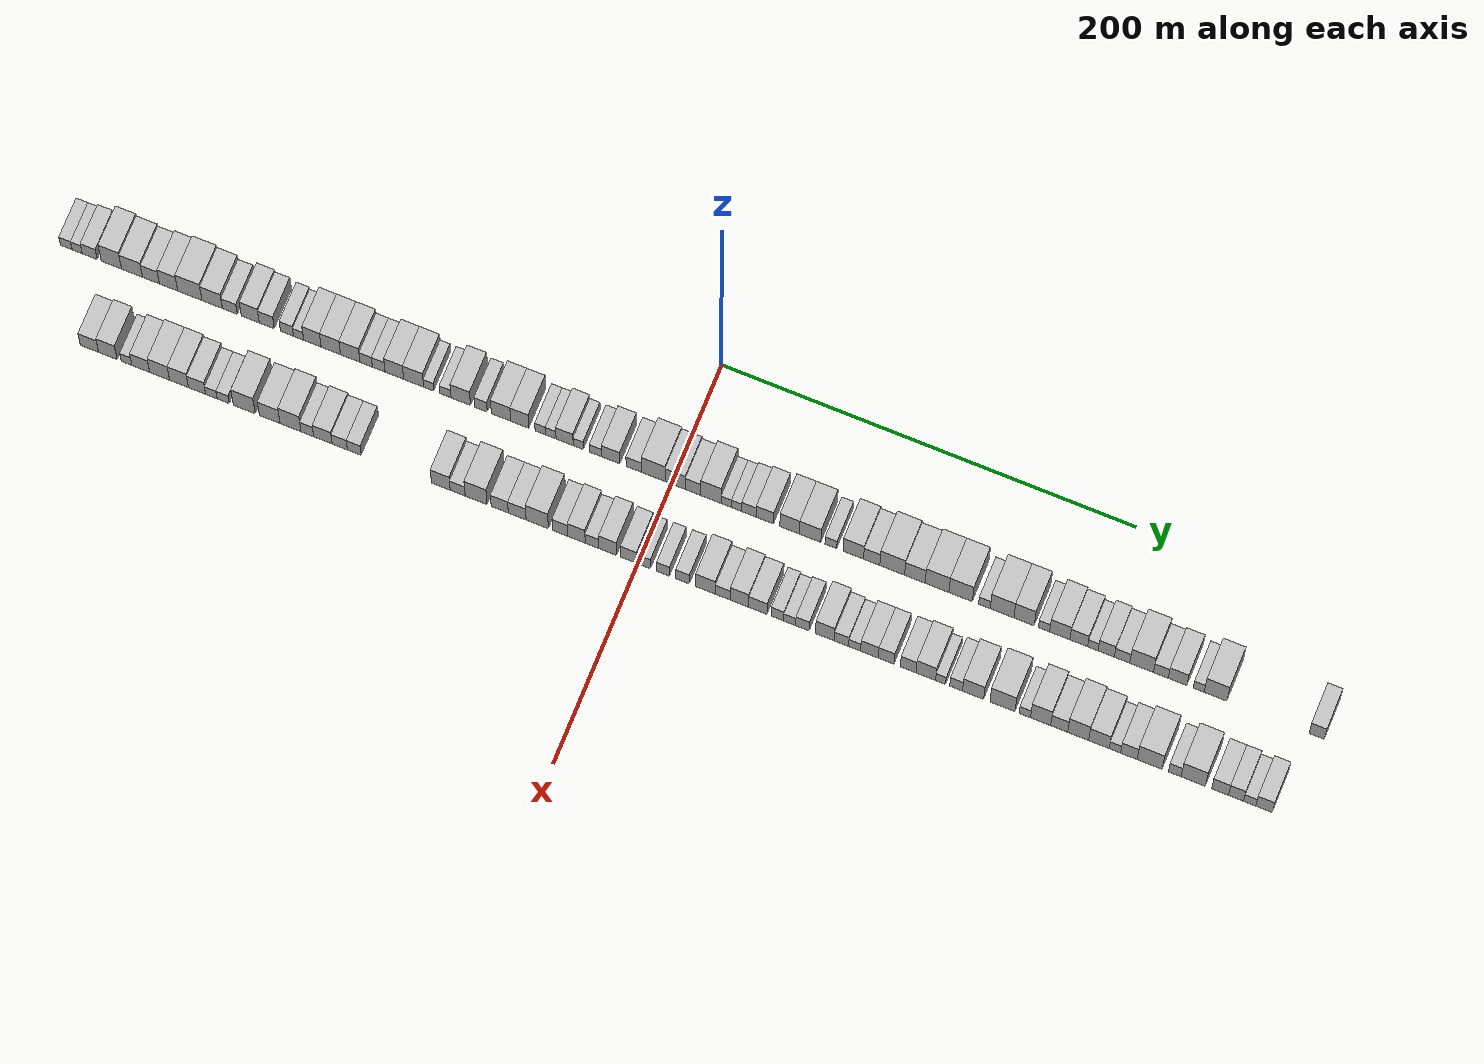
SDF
<sdf version="1.6">
 <world name="default">
  <scene>
   <sky><clouds><speed>12</speed></clouds></sky>
   <ambient>0.4 0.4 0.4 1</ambient>
   <background>0.7 0.7 0.7 1</background>
   <shadows>1</shadows>
  </scene>
  <gravity>0 0 -9.8066</gravity>
  <magnetic_field>6e-06 2.3e-05 -4.2e-05</magnetic_field>
  <physics default="0" name="default_physics" type="ode">
   <ode>
    <solver>
     <type>quick</type>
     <iters>10</iters>
     <sor>1.0</sor>
     <use_dynamic_moi_rescaling>0</use_dynamic_moi_rescaling>
    </solver>
    <constraints>
     <cfm>0</cfm>
     <erp>0.2</erp>
     <contact_max_correcting_vel>100</contact_max_correcting_vel>
     <contact_surface_layer>0.001</contact_surface_layer>
    </constraints>
   </ode>
   <max_step_size>0.004</max_step_size>
   <real_time_factor>1</real_time_factor>
   <real_time_update_rate>250</real_time_update_rate>
  </physics>
  <light name="sun" type="directional">
   <pose>0 0 10 0 0 0</pose>
   <diffuse>0.8 0.8 0.8 1</diffuse>
   <specular>0.2 0.2 0.2 1</specular>
   <attenuation>
    <range>1000</range>
    <constant>0.9</constant>
    <linear>0.01</linear>
    <quadratic>0.001</quadratic>
   </attenuation>
   <direction>-0.5 0.1 -0.9</direction>
  </light>
  <model name="building_1">
   <static>1</static>
   <pose>50.0000 -295.1199 0 0.000000 0.000000 0.000000</pose>
   <link name="link">
    <pose>0 0 6.00 0 0 0</pose>
    <collision name="collision"><geometry><box><size>20.0000 5.7602 12.0000</size></box></geometry></collision>
    <visual name="visual">
     <cast_shadows>0</cast_shadows>
     <geometry><box><size>20.0000 5.7602 12.0000</size></box></geometry>
     <material>
      <script>
       <uri>model://HANNAS_wall/materials/scripts</uri>
       <uri>model://HANNAS_wall/materials/textures</uri>
       <name>vrc/HANNAS_wall</name>
      </script>
     </material>
    </visual>
   </link>
  </model>
  <model name="building_2">
   <static>1</static>
   <pose>50.0000 -289.7702 0 0.000000 0.000000 0.000000</pose>
   <link name="link">
    <pose>0 0 6.00 0 0 0</pose>
    <collision name="collision"><geometry><box><size>20.0000 4.9393 12.0000</size></box></geometry></collision>
    <visual name="visual">
     <cast_shadows>0</cast_shadows>
     <geometry><box><size>20.0000 4.9393 12.0000</size></box></geometry>
     <material>
      <script>
       <uri>model://HANNAS_wall/materials/scripts</uri>
       <uri>model://HANNAS_wall/materials/textures</uri>
       <name>vrc/HANNAS_wall</name>
      </script>
     </material>
    </visual>
   </link>
  </model>
  <model name="building_3">
   <static>1</static>
   <pose>50.0000 -283.6159 0 0.000000 0.000000 0.000000</pose>
   <link name="link">
    <pose>0 0 7.50 0 0 0</pose>
    <collision name="collision"><geometry><box><size>20.0000 7.3694 15.0000</size></box></geometry></collision>
    <visual name="visual">
     <cast_shadows>0</cast_shadows>
     <geometry><box><size>20.0000 7.3694 15.0000</size></box></geometry>
     <material>
      <script>
       <uri>model://HANNAS_wall/materials/scripts</uri>
       <uri>model://HANNAS_wall/materials/textures</uri>
       <name>vrc/HANNAS_wall</name>
      </script>
     </material>
    </visual>
   </link>
  </model>
  <model name="building_4">
   <static>1</static>
   <pose>50.0000 -272.9616 0 0.000000 0.000000 0.000000</pose>
   <link name="link">
    <pose>0 0 12.00 0 0 0</pose>
    <collision name="collision"><geometry><box><size>20.0000 9.9390 24.0000</size></box></geometry></collision>
    <visual name="visual">
     <cast_shadows>0</cast_shadows>
     <geometry><box><size>20.0000 9.9390 24.0000</size></box></geometry>
     <material>
      <script>
       <uri>model://HANNAS_wall/materials/scripts</uri>
       <uri>model://HANNAS_wall/materials/textures</uri>
       <name>vrc/HANNAS_wall</name>
      </script>
     </material>
    </visual>
   </link>
  </model>
  <model name="building_5">
   <static>1</static>
   <pose>50.0000 -262.8391 0 0.000000 0.000000 0.000000</pose>
   <link name="link">
    <pose>0 0 10.50 0 0 0</pose>
    <collision name="collision"><geometry><box><size>20.0000 10.3061 21.0000</size></box></geometry></collision>
    <visual name="visual">
     <cast_shadows>0</cast_shadows>
     <geometry><box><size>20.0000 10.3061 21.0000</size></box></geometry>
     <material>
      <script>
       <uri>model://HANNAS_wall/materials/scripts</uri>
       <uri>model://HANNAS_wall/materials/textures</uri>
       <name>vrc/HANNAS_wall</name>
      </script>
     </material>
    </visual>
   </link>
  </model>
  <model name="building_6">
   <static>1</static>
   <pose>50.0000 -253.5562 0 0.000000 0.000000 0.000000</pose>
   <link name="link">
    <pose>0 0 9.00 0 0 0</pose>
    <collision name="collision"><geometry><box><size>20.0000 8.2598 18.0000</size></box></geometry></collision>
    <visual name="visual">
     <cast_shadows>0</cast_shadows>
     <geometry><box><size>20.0000 8.2598 18.0000</size></box></geometry>
     <material>
      <script>
       <uri>model://HANNAS_wall/materials/scripts</uri>
       <uri>model://HANNAS_wall/materials/textures</uri>
       <name>vrc/HANNAS_wall</name>
      </script>
     </material>
    </visual>
   </link>
  </model>
  <model name="building_7">
   <static>1</static>
   <pose>50.0000 -244.9566 0 0.000000 0.000000 0.000000</pose>
   <link name="link">
    <pose>0 0 10.50 0 0 0</pose>
    <collision name="collision"><geometry><box><size>20.0000 8.9393 21.0000</size></box></geometry></collision>
    <visual name="visual">
     <cast_shadows>0</cast_shadows>
     <geometry><box><size>20.0000 8.9393 21.0000</size></box></geometry>
     <material>
      <script>
       <uri>model://HANNAS_wall/materials/scripts</uri>
       <uri>model://HANNAS_wall/materials/textures</uri>
       <name>vrc/HANNAS_wall</name>
      </script>
     </material>
    </visual>
   </link>
  </model>
  <model name="building_8">
   <static>1</static>
   <pose>50.0000 -234.5517 0 0.000000 0.000000 0.000000</pose>
   <link name="link">
    <pose>0 0 12.00 0 0 0</pose>
    <collision name="collision"><geometry><box><size>20.0000 11.8707 24.0000</size></box></geometry></collision>
    <visual name="visual">
     <cast_shadows>0</cast_shadows>
     <geometry><box><size>20.0000 11.8707 24.0000</size></box></geometry>
     <material>
      <script>
       <uri>model://HANNAS_wall/materials/scripts</uri>
       <uri>model://HANNAS_wall/materials/textures</uri>
       <name>vrc/HANNAS_wall</name>
      </script>
     </material>
    </visual>
   </link>
  </model>
  <model name="building_9">
   <static>1</static>
   <pose>50.0000 -223.6059 0 0.000000 0.000000 0.000000</pose>
   <link name="link">
    <pose>0 0 10.50 0 0 0</pose>
    <collision name="collision"><geometry><box><size>20.0000 10.0209 21.0000</size></box></geometry></collision>
    <visual name="visual">
     <cast_shadows>0</cast_shadows>
     <geometry><box><size>20.0000 10.0209 21.0000</size></box></geometry>
     <material>
      <script>
       <uri>model://HANNAS_wall/materials/scripts</uri>
       <uri>model://HANNAS_wall/materials/textures</uri>
       <name>vrc/HANNAS_wall</name>
      </script>
     </material>
    </visual>
   </link>
  </model>
  <model name="building_10">
   <static>1</static>
   <pose>50.0000 -214.9441 0 0.000000 0.000000 0.000000</pose>
   <link name="link">
    <pose>0 0 7.50 0 0 0</pose>
    <collision name="collision"><geometry><box><size>20.0000 7.3027 15.0000</size></box></geometry></collision>
    <visual name="visual">
     <cast_shadows>0</cast_shadows>
     <geometry><box><size>20.0000 7.3027 15.0000</size></box></geometry>
     <material>
      <script>
       <uri>model://HANNAS_wall/materials/scripts</uri>
       <uri>model://HANNAS_wall/materials/textures</uri>
       <name>vrc/HANNAS_wall</name>
      </script>
     </material>
    </visual>
   </link>
  </model>
  <model name="building_11">
   <static>1</static>
   <pose>50.0000 -204.8995 0 0.000000 0.000000 0.000000</pose>
   <link name="link">
    <pose>0 0 10.50 0 0 0</pose>
    <collision name="collision"><geometry><box><size>20.0000 8.7866 21.0000</size></box></geometry></collision>
    <visual name="visual">
     <cast_shadows>0</cast_shadows>
     <geometry><box><size>20.0000 8.7866 21.0000</size></box></geometry>
     <material>
      <script>
       <uri>model://HANNAS_wall/materials/scripts</uri>
       <uri>model://HANNAS_wall/materials/textures</uri>
       <name>vrc/HANNAS_wall</name>
      </script>
     </material>
    </visual>
   </link>
  </model>
  <model name="building_12">
   <static>1</static>
   <pose>50.0000 -196.8550 0 0.000000 0.000000 0.000000</pose>
   <link name="link">
    <pose>0 0 9.00 0 0 0</pose>
    <collision name="collision"><geometry><box><size>20.0000 7.3025 18.0000</size></box></geometry></collision>
    <visual name="visual">
     <cast_shadows>0</cast_shadows>
     <geometry><box><size>20.0000 7.3025 18.0000</size></box></geometry>
     <material>
      <script>
       <uri>model://HANNAS_wall/materials/scripts</uri>
       <uri>model://HANNAS_wall/materials/textures</uri>
       <name>vrc/HANNAS_wall</name>
      </script>
     </material>
    </visual>
   </link>
  </model>
  <model name="building_13">
   <static>1</static>
   <pose>50.0000 -187.0091 0 0.000000 0.000000 0.000000</pose>
   <link name="link">
    <pose>0 0 7.50 0 0 0</pose>
    <collision name="collision"><geometry><box><size>20.0000 6.3892 15.0000</size></box></geometry></collision>
    <visual name="visual">
     <cast_shadows>0</cast_shadows>
     <geometry><box><size>20.0000 6.3892 15.0000</size></box></geometry>
     <material>
      <script>
       <uri>model://HANNAS_wall/materials/scripts</uri>
       <uri>model://HANNAS_wall/materials/textures</uri>
       <name>vrc/HANNAS_wall</name>
      </script>
     </material>
    </visual>
   </link>
  </model>
  <model name="building_14">
   <static>1</static>
   <pose>50.0000 -181.3262 0 0.000000 0.000000 0.000000</pose>
   <link name="link">
    <pose>0 0 6.00 0 0 0</pose>
    <collision name="collision"><geometry><box><size>20.0000 4.9767 12.0000</size></box></geometry></collision>
    <visual name="visual">
     <cast_shadows>0</cast_shadows>
     <geometry><box><size>20.0000 4.9767 12.0000</size></box></geometry>
     <material>
      <script>
       <uri>model://HANNAS_wall/materials/scripts</uri>
       <uri>model://HANNAS_wall/materials/textures</uri>
       <name>vrc/HANNAS_wall</name>
      </script>
     </material>
    </visual>
   </link>
  </model>
  <model name="building_15">
   <static>1</static>
   <pose>50.0000 -174.5709 0 0.000000 0.000000 0.000000</pose>
   <link name="link">
    <pose>0 0 10.50 0 0 0</pose>
    <collision name="collision"><geometry><box><size>20.0000 8.5340 21.0000</size></box></geometry></collision>
    <visual name="visual">
     <cast_shadows>0</cast_shadows>
     <geometry><box><size>20.0000 8.5340 21.0000</size></box></geometry>
     <material>
      <script>
       <uri>model://HANNAS_wall/materials/scripts</uri>
       <uri>model://HANNAS_wall/materials/textures</uri>
       <name>vrc/HANNAS_wall</name>
      </script>
     </material>
    </visual>
   </link>
  </model>
  <model name="building_16">
   <static>1</static>
   <pose>50.0000 -165.5938 0 0.000000 0.000000 0.000000</pose>
   <link name="link">
    <pose>0 0 10.50 0 0 0</pose>
    <collision name="collision"><geometry><box><size>20.0000 9.4202 21.0000</size></box></geometry></collision>
    <visual name="visual">
     <cast_shadows>0</cast_shadows>
     <geometry><box><size>20.0000 9.4202 21.0000</size></box></geometry>
     <material>
      <script>
       <uri>model://HANNAS_wall/materials/scripts</uri>
       <uri>model://HANNAS_wall/materials/textures</uri>
       <name>vrc/HANNAS_wall</name>
      </script>
     </material>
    </visual>
   </link>
  </model>
  <model name="building_17">
   <static>1</static>
   <pose>50.0000 -156.1160 0 0.000000 0.000000 0.000000</pose>
   <link name="link">
    <pose>0 0 10.50 0 0 0</pose>
    <collision name="collision"><geometry><box><size>20.0000 9.5353 21.0000</size></box></geometry></collision>
    <visual name="visual">
     <cast_shadows>0</cast_shadows>
     <geometry><box><size>20.0000 9.5353 21.0000</size></box></geometry>
     <material>
      <script>
       <uri>model://HANNAS_wall/materials/scripts</uri>
       <uri>model://HANNAS_wall/materials/textures</uri>
       <name>vrc/HANNAS_wall</name>
      </script>
     </material>
    </visual>
   </link>
  </model>
  <model name="building_18">
   <static>1</static>
   <pose>50.0000 -148.3385 0 0.000000 0.000000 0.000000</pose>
   <link name="link">
    <pose>0 0 7.50 0 0 0</pose>
    <collision name="collision"><geometry><box><size>20.0000 6.0197 15.0000</size></box></geometry></collision>
    <visual name="visual">
     <cast_shadows>0</cast_shadows>
     <geometry><box><size>20.0000 6.0197 15.0000</size></box></geometry>
     <material>
      <script>
       <uri>model://HANNAS_wall/materials/scripts</uri>
       <uri>model://HANNAS_wall/materials/textures</uri>
       <name>vrc/HANNAS_wall</name>
      </script>
     </material>
    </visual>
   </link>
  </model>
  <model name="building_19">
   <static>1</static>
   <pose>50.0000 -142.2222 0 0.000000 0.000000 0.000000</pose>
   <link name="link">
    <pose>0 0 7.50 0 0 0</pose>
    <collision name="collision"><geometry><box><size>20.0000 6.2130 15.0000</size></box></geometry></collision>
    <visual name="visual">
     <cast_shadows>0</cast_shadows>
     <geometry><box><size>20.0000 6.2130 15.0000</size></box></geometry>
     <material>
      <script>
       <uri>model://HANNAS_wall/materials/scripts</uri>
       <uri>model://HANNAS_wall/materials/textures</uri>
       <name>vrc/HANNAS_wall</name>
      </script>
     </material>
    </visual>
   </link>
  </model>
  <model name="building_20">
   <static>1</static>
   <pose>50.0000 -134.5825 0 0.000000 0.000000 0.000000</pose>
   <link name="link">
    <pose>0 0 10.50 0 0 0</pose>
    <collision name="collision"><geometry><box><size>20.0000 9.0664 21.0000</size></box></geometry></collision>
    <visual name="visual">
     <cast_shadows>0</cast_shadows>
     <geometry><box><size>20.0000 9.0664 21.0000</size></box></geometry>
     <material>
      <script>
       <uri>model://HANNAS_wall/materials/scripts</uri>
       <uri>model://HANNAS_wall/materials/textures</uri>
       <name>vrc/HANNAS_wall</name>
      </script>
     </material>
    </visual>
   </link>
  </model>
  <model name="building_21">
   <static>1</static>
   <pose>50.0000 -125.1718 0 0.000000 0.000000 0.000000</pose>
   <link name="link">
    <pose>0 0 10.50 0 0 0</pose>
    <collision name="collision"><geometry><box><size>20.0000 9.7550 21.0000</size></box></geometry></collision>
    <visual name="visual">
     <cast_shadows>0</cast_shadows>
     <geometry><box><size>20.0000 9.7550 21.0000</size></box></geometry>
     <material>
      <script>
       <uri>model://HANNAS_wall/materials/scripts</uri>
       <uri>model://HANNAS_wall/materials/textures</uri>
       <name>vrc/HANNAS_wall</name>
      </script>
     </material>
    </visual>
   </link>
  </model>
  <model name="building_22">
   <static>1</static>
   <pose>50.0000 -117.8900 0 0.000000 0.000000 0.000000</pose>
   <link name="link">
    <pose>0 0 6.00 0 0 0</pose>
    <collision name="collision"><geometry><box><size>20.0000 4.8085 12.0000</size></box></geometry></collision>
    <visual name="visual">
     <cast_shadows>0</cast_shadows>
     <geometry><box><size>20.0000 4.8085 12.0000</size></box></geometry>
     <material>
      <script>
       <uri>model://HANNAS_wall/materials/scripts</uri>
       <uri>model://HANNAS_wall/materials/textures</uri>
       <name>vrc/HANNAS_wall</name>
      </script>
     </material>
    </visual>
   </link>
  </model>
  <model name="building_23">
   <static>1</static>
   <pose>50.0000 -109.7450 0 0.000000 0.000000 0.000000</pose>
   <link name="link">
    <pose>0 0 6.00 0 0 0</pose>
    <collision name="collision"><geometry><box><size>20.0000 5.4815 12.0000</size></box></geometry></collision>
    <visual name="visual">
     <cast_shadows>0</cast_shadows>
     <geometry><box><size>20.0000 5.4815 12.0000</size></box></geometry>
     <material>
      <script>
       <uri>model://HANNAS_wall/materials/scripts</uri>
       <uri>model://HANNAS_wall/materials/textures</uri>
       <name>vrc/HANNAS_wall</name>
      </script>
     </material>
    </visual>
   </link>
  </model>
  <model name="building_24">
   <static>1</static>
   <pose>50.0000 -102.2706 0 0.000000 0.000000 0.000000</pose>
   <link name="link">
    <pose>0 0 10.50 0 0 0</pose>
    <collision name="collision"><geometry><box><size>20.0000 9.4674 21.0000</size></box></geometry></collision>
    <visual name="visual">
     <cast_shadows>0</cast_shadows>
     <geometry><box><size>20.0000 9.4674 21.0000</size></box></geometry>
     <material>
      <script>
       <uri>model://HANNAS_wall/materials/scripts</uri>
       <uri>model://HANNAS_wall/materials/textures</uri>
       <name>vrc/HANNAS_wall</name>
      </script>
     </material>
    </visual>
   </link>
  </model>
  <model name="building_25">
   <static>1</static>
   <pose>50.0000 -92.4875 0 0.000000 0.000000 0.000000</pose>
   <link name="link">
    <pose>0 0 7.50 0 0 0</pose>
    <collision name="collision"><geometry><box><size>20.0000 6.0987 15.0000</size></box></geometry></collision>
    <visual name="visual">
     <cast_shadows>0</cast_shadows>
     <geometry><box><size>20.0000 6.0987 15.0000</size></box></geometry>
     <material>
      <script>
       <uri>model://HANNAS_wall/materials/scripts</uri>
       <uri>model://HANNAS_wall/materials/textures</uri>
       <name>vrc/HANNAS_wall</name>
      </script>
     </material>
    </visual>
   </link>
  </model>
  <model name="building_26">
   <static>1</static>
   <pose>50.0000 -82.7279 0 0.000000 0.000000 0.000000</pose>
   <link name="link">
    <pose>0 0 10.50 0 0 0</pose>
    <collision name="collision"><geometry><box><size>20.0000 9.4206 21.0000</size></box></geometry></collision>
    <visual name="visual">
     <cast_shadows>0</cast_shadows>
     <geometry><box><size>20.0000 9.4206 21.0000</size></box></geometry>
     <material>
      <script>
       <uri>model://HANNAS_wall/materials/scripts</uri>
       <uri>model://HANNAS_wall/materials/textures</uri>
       <name>vrc/HANNAS_wall</name>
      </script>
     </material>
    </visual>
   </link>
  </model>
  <model name="building_27">
   <static>1</static>
   <pose>50.0000 -73.6038 0 0.000000 0.000000 0.000000</pose>
   <link name="link">
    <pose>0 0 10.50 0 0 0</pose>
    <collision name="collision"><geometry><box><size>20.0000 8.8276 21.0000</size></box></geometry></collision>
    <visual name="visual">
     <cast_shadows>0</cast_shadows>
     <geometry><box><size>20.0000 8.8276 21.0000</size></box></geometry>
     <material>
      <script>
       <uri>model://HANNAS_wall/materials/scripts</uri>
       <uri>model://HANNAS_wall/materials/textures</uri>
       <name>vrc/HANNAS_wall</name>
      </script>
     </material>
    </visual>
   </link>
  </model>
  <model name="building_28">
   <static>1</static>
   <pose>50.0000 -63.6150 0 0.000000 0.000000 0.000000</pose>
   <link name="link">
    <pose>0 0 6.00 0 0 0</pose>
    <collision name="collision"><geometry><box><size>20.0000 5.1499 12.0000</size></box></geometry></collision>
    <visual name="visual">
     <cast_shadows>0</cast_shadows>
     <geometry><box><size>20.0000 5.1499 12.0000</size></box></geometry>
     <material>
      <script>
       <uri>model://HANNAS_wall/materials/scripts</uri>
       <uri>model://HANNAS_wall/materials/textures</uri>
       <name>vrc/HANNAS_wall</name>
      </script>
     </material>
    </visual>
   </link>
  </model>
  <model name="building_29">
   <static>1</static>
   <pose>50.0000 -58.5126 0 0.000000 0.000000 0.000000</pose>
   <link name="link">
    <pose>0 0 6.00 0 0 0</pose>
    <collision name="collision"><geometry><box><size>20.0000 5.0548 12.0000</size></box></geometry></collision>
    <visual name="visual">
     <cast_shadows>0</cast_shadows>
     <geometry><box><size>20.0000 5.0548 12.0000</size></box></geometry>
     <material>
      <script>
       <uri>model://HANNAS_wall/materials/scripts</uri>
       <uri>model://HANNAS_wall/materials/textures</uri>
       <name>vrc/HANNAS_wall</name>
      </script>
     </material>
    </visual>
   </link>
  </model>
  <model name="building_30">
   <static>1</static>
   <pose>50.0000 -51.8167 0 0.000000 0.000000 0.000000</pose>
   <link name="link">
    <pose>0 0 9.00 0 0 0</pose>
    <collision name="collision"><geometry><box><size>20.0000 8.3369 18.0000</size></box></geometry></collision>
    <visual name="visual">
     <cast_shadows>0</cast_shadows>
     <geometry><box><size>20.0000 8.3369 18.0000</size></box></geometry>
     <material>
      <script>
       <uri>model://HANNAS_wall/materials/scripts</uri>
       <uri>model://HANNAS_wall/materials/textures</uri>
       <name>vrc/HANNAS_wall</name>
      </script>
     </material>
    </visual>
   </link>
  </model>
  <model name="building_31">
   <static>1</static>
   <pose>50.0000 -45.2195 0 0.000000 0.000000 0.000000</pose>
   <link name="link">
    <pose>0 0 6.00 0 0 0</pose>
    <collision name="collision"><geometry><box><size>20.0000 4.8577 12.0000</size></box></geometry></collision>
    <visual name="visual">
     <cast_shadows>0</cast_shadows>
     <geometry><box><size>20.0000 4.8577 12.0000</size></box></geometry>
     <material>
      <script>
       <uri>model://HANNAS_wall/materials/scripts</uri>
       <uri>model://HANNAS_wall/materials/textures</uri>
       <name>vrc/HANNAS_wall</name>
      </script>
     </material>
    </visual>
   </link>
  </model>
  <model name="building_32">
   <static>1</static>
   <pose>50.0000 -36.8826 0 0.000000 0.000000 0.000000</pose>
   <link name="link">
    <pose>0 0 6.00 0 0 0</pose>
    <collision name="collision"><geometry><box><size>20.0000 5.8160 12.0000</size></box></geometry></collision>
    <visual name="visual">
     <cast_shadows>0</cast_shadows>
     <geometry><box><size>20.0000 5.8160 12.0000</size></box></geometry>
     <material>
      <script>
       <uri>model://HANNAS_wall/materials/scripts</uri>
       <uri>model://HANNAS_wall/materials/textures</uri>
       <name>vrc/HANNAS_wall</name>
      </script>
     </material>
    </visual>
   </link>
  </model>
  <model name="building_33">
   <static>1</static>
   <pose>50.0000 -29.4980 0 0.000000 0.000000 0.000000</pose>
   <link name="link">
    <pose>0 0 9.00 0 0 0</pose>
    <collision name="collision"><geometry><box><size>20.0000 8.9532 18.0000</size></box></geometry></collision>
    <visual name="visual">
     <cast_shadows>0</cast_shadows>
     <geometry><box><size>20.0000 8.9532 18.0000</size></box></geometry>
     <material>
      <script>
       <uri>model://HANNAS_wall/materials/scripts</uri>
       <uri>model://HANNAS_wall/materials/textures</uri>
       <name>vrc/HANNAS_wall</name>
      </script>
     </material>
    </visual>
   </link>
  </model>
  <model name="building_34">
   <static>1</static>
   <pose>50.0000 -18.2981 0 0.000000 0.000000 0.000000</pose>
   <link name="link">
    <pose>0 0 7.50 0 0 0</pose>
    <collision name="collision"><geometry><box><size>20.0000 7.4467 15.0000</size></box></geometry></collision>
    <visual name="visual">
     <cast_shadows>0</cast_shadows>
     <geometry><box><size>20.0000 7.4467 15.0000</size></box></geometry>
     <material>
      <script>
       <uri>model://HANNAS_wall/materials/scripts</uri>
       <uri>model://HANNAS_wall/materials/textures</uri>
       <name>vrc/HANNAS_wall</name>
      </script>
     </material>
    </visual>
   </link>
  </model>
  <model name="building_35">
   <static>1</static>
   <pose>50.0000 -8.8519 0 0.000000 0.000000 0.000000</pose>
   <link name="link">
    <pose>0 0 12.00 0 0 0</pose>
    <collision name="collision"><geometry><box><size>20.0000 11.4456 24.0000</size></box></geometry></collision>
    <visual name="visual">
     <cast_shadows>0</cast_shadows>
     <geometry><box><size>20.0000 11.4456 24.0000</size></box></geometry>
     <material>
      <script>
       <uri>model://HANNAS_wall/materials/scripts</uri>
       <uri>model://HANNAS_wall/materials/textures</uri>
       <name>vrc/HANNAS_wall</name>
      </script>
     </material>
    </visual>
   </link>
  </model>
  <model name="building_36">
   <static>1</static>
   <pose>50.0000 1.7519 0 0.000000 0.000000 0.000000</pose>
   <link name="link">
    <pose>0 0 10.50 0 0 0</pose>
    <collision name="collision"><geometry><box><size>20.0000 9.7621 21.0000</size></box></geometry></collision>
    <visual name="visual">
     <cast_shadows>0</cast_shadows>
     <geometry><box><size>20.0000 9.7621 21.0000</size></box></geometry>
     <material>
      <script>
       <uri>model://HANNAS_wall/materials/scripts</uri>
       <uri>model://HANNAS_wall/materials/textures</uri>
       <name>vrc/HANNAS_wall</name>
      </script>
     </material>
    </visual>
   </link>
  </model>
  <model name="building_37">
   <static>1</static>
   <pose>50.0000 10.3799 0 0.000000 0.000000 0.000000</pose>
   <link name="link">
    <pose>0 0 9.00 0 0 0</pose>
    <collision name="collision"><geometry><box><size>20.0000 7.4938 18.0000</size></box></geometry></collision>
    <visual name="visual">
     <cast_shadows>0</cast_shadows>
     <geometry><box><size>20.0000 7.4938 18.0000</size></box></geometry>
     <material>
      <script>
       <uri>model://HANNAS_wall/materials/scripts</uri>
       <uri>model://HANNAS_wall/materials/textures</uri>
       <name>vrc/HANNAS_wall</name>
      </script>
     </material>
    </visual>
   </link>
  </model>
  <model name="building_38">
   <static>1</static>
   <pose>50.0000 19.0260 0 0.000000 0.000000 0.000000</pose>
   <link name="link">
    <pose>0 0 12.00 0 0 0</pose>
    <collision name="collision"><geometry><box><size>20.0000 9.7985 24.0000</size></box></geometry></collision>
    <visual name="visual">
     <cast_shadows>0</cast_shadows>
     <geometry><box><size>20.0000 9.7985 24.0000</size></box></geometry>
     <material>
      <script>
       <uri>model://HANNAS_wall/materials/scripts</uri>
       <uri>model://HANNAS_wall/materials/textures</uri>
       <name>vrc/HANNAS_wall</name>
      </script>
     </material>
    </visual>
   </link>
  </model>
  <model name="building_39">
   <static>1</static>
   <pose>50.0000 26.4072 0 0.000000 0.000000 0.000000</pose>
   <link name="link">
    <pose>0 0 6.00 0 0 0</pose>
    <collision name="collision"><geometry><box><size>20.0000 4.9640 12.0000</size></box></geometry></collision>
    <visual name="visual">
     <cast_shadows>0</cast_shadows>
     <geometry><box><size>20.0000 4.9640 12.0000</size></box></geometry>
     <material>
      <script>
       <uri>model://HANNAS_wall/materials/scripts</uri>
       <uri>model://HANNAS_wall/materials/textures</uri>
       <name>vrc/HANNAS_wall</name>
      </script>
     </material>
    </visual>
   </link>
  </model>
  <model name="building_40">
   <static>1</static>
   <pose>50.0000 31.3731 0 0.000000 0.000000 0.000000</pose>
   <link name="link">
    <pose>0 0 6.00 0 0 0</pose>
    <collision name="collision"><geometry><box><size>20.0000 4.9677 12.0000</size></box></geometry></collision>
    <visual name="visual">
     <cast_shadows>0</cast_shadows>
     <geometry><box><size>20.0000 4.9677 12.0000</size></box></geometry>
     <material>
      <script>
       <uri>model://HANNAS_wall/materials/scripts</uri>
       <uri>model://HANNAS_wall/materials/textures</uri>
       <name>vrc/HANNAS_wall</name>
      </script>
     </material>
    </visual>
   </link>
  </model>
  <model name="building_41">
   <static>1</static>
   <pose>50.0000 37.3386 0 0.000000 0.000000 0.000000</pose>
   <link name="link">
    <pose>0 0 7.50 0 0 0</pose>
    <collision name="collision"><geometry><box><size>20.0000 6.9632 15.0000</size></box></geometry></collision>
    <visual name="visual">
     <cast_shadows>0</cast_shadows>
     <geometry><box><size>20.0000 6.9632 15.0000</size></box></geometry>
     <material>
      <script>
       <uri>model://HANNAS_wall/materials/scripts</uri>
       <uri>model://HANNAS_wall/materials/textures</uri>
       <name>vrc/HANNAS_wall</name>
      </script>
     </material>
    </visual>
   </link>
  </model>
  <model name="building_42">
   <static>1</static>
   <pose>50.0000 45.0478 0 0.000000 0.000000 0.000000</pose>
   <link name="link">
    <pose>0 0 9.00 0 0 0</pose>
    <collision name="collision"><geometry><box><size>20.0000 8.4552 18.0000</size></box></geometry></collision>
    <visual name="visual">
     <cast_shadows>0</cast_shadows>
     <geometry><box><size>20.0000 8.4552 18.0000</size></box></geometry>
     <material>
      <script>
       <uri>model://HANNAS_wall/materials/scripts</uri>
       <uri>model://HANNAS_wall/materials/textures</uri>
       <name>vrc/HANNAS_wall</name>
      </script>
     </material>
    </visual>
   </link>
  </model>
  <model name="building_43">
   <static>1</static>
   <pose>50.0000 56.9796 0 0.000000 0.000000 0.000000</pose>
   <link name="link">
    <pose>0 0 10.50 0 0 0</pose>
    <collision name="collision"><geometry><box><size>20.0000 9.4084 21.0000</size></box></geometry></collision>
    <visual name="visual">
     <cast_shadows>0</cast_shadows>
     <geometry><box><size>20.0000 9.4084 21.0000</size></box></geometry>
     <material>
      <script>
       <uri>model://HANNAS_wall/materials/scripts</uri>
       <uri>model://HANNAS_wall/materials/textures</uri>
       <name>vrc/HANNAS_wall</name>
      </script>
     </material>
    </visual>
   </link>
  </model>
  <model name="building_44">
   <static>1</static>
   <pose>50.0000 66.8677 0 0.000000 0.000000 0.000000</pose>
   <link name="link">
    <pose>0 0 10.50 0 0 0</pose>
    <collision name="collision"><geometry><box><size>20.0000 10.3678 21.0000</size></box></geometry></collision>
    <visual name="visual">
     <cast_shadows>0</cast_shadows>
     <geometry><box><size>20.0000 10.3678 21.0000</size></box></geometry>
     <material>
      <script>
       <uri>model://HANNAS_wall/materials/scripts</uri>
       <uri>model://HANNAS_wall/materials/textures</uri>
       <name>vrc/HANNAS_wall</name>
      </script>
     </material>
    </visual>
   </link>
  </model>
  <model name="building_45">
   <static>1</static>
   <pose>50.0000 76.8989 0 0.000000 0.000000 0.000000</pose>
   <link name="link">
    <pose>0 0 6.00 0 0 0</pose>
    <collision name="collision"><geometry><box><size>20.0000 5.6946 12.0000</size></box></geometry></collision>
    <visual name="visual">
     <cast_shadows>0</cast_shadows>
     <geometry><box><size>20.0000 5.6946 12.0000</size></box></geometry>
     <material>
      <script>
       <uri>model://HANNAS_wall/materials/scripts</uri>
       <uri>model://HANNAS_wall/materials/textures</uri>
       <name>vrc/HANNAS_wall</name>
      </script>
     </material>
    </visual>
   </link>
  </model>
  <model name="building_46">
   <static>1</static>
   <pose>50.0000 87.6956 0 0.000000 0.000000 0.000000</pose>
   <link name="link">
    <pose>0 0 10.50 0 0 0</pose>
    <collision name="collision"><geometry><box><size>20.0000 9.8988 21.0000</size></box></geometry></collision>
    <visual name="visual">
     <cast_shadows>0</cast_shadows>
     <geometry><box><size>20.0000 9.8988 21.0000</size></box></geometry>
     <material>
      <script>
       <uri>model://HANNAS_wall/materials/scripts</uri>
       <uri>model://HANNAS_wall/materials/textures</uri>
       <name>vrc/HANNAS_wall</name>
      </script>
     </material>
    </visual>
   </link>
  </model>
  <model name="building_47">
   <static>1</static>
   <pose>50.0000 96.5750 0 0.000000 0.000000 0.000000</pose>
   <link name="link">
    <pose>0 0 9.00 0 0 0</pose>
    <collision name="collision"><geometry><box><size>20.0000 7.8600 18.0000</size></box></geometry></collision>
    <visual name="visual">
     <cast_shadows>0</cast_shadows>
     <geometry><box><size>20.0000 7.8600 18.0000</size></box></geometry>
     <material>
      <script>
       <uri>model://HANNAS_wall/materials/scripts</uri>
       <uri>model://HANNAS_wall/materials/textures</uri>
       <name>vrc/HANNAS_wall</name>
      </script>
     </material>
    </visual>
   </link>
  </model>
  <model name="building_48">
   <static>1</static>
   <pose>50.0000 106.4544 0 0.000000 0.000000 0.000000</pose>
   <link name="link">
    <pose>0 0 12.00 0 0 0</pose>
    <collision name="collision"><geometry><box><size>20.0000 11.8987 24.0000</size></box></geometry></collision>
    <visual name="visual">
     <cast_shadows>0</cast_shadows>
     <geometry><box><size>20.0000 11.8987 24.0000</size></box></geometry>
     <material>
      <script>
       <uri>model://HANNAS_wall/materials/scripts</uri>
       <uri>model://HANNAS_wall/materials/textures</uri>
       <name>vrc/HANNAS_wall</name>
      </script>
     </material>
    </visual>
   </link>
  </model>
  <model name="building_49">
   <static>1</static>
   <pose>50.0000 117.3577 0 0.000000 0.000000 0.000000</pose>
   <link name="link">
    <pose>0 0 10.50 0 0 0</pose>
    <collision name="collision"><geometry><box><size>20.0000 9.9080 21.0000</size></box></geometry></collision>
    <visual name="visual">
     <cast_shadows>0</cast_shadows>
     <geometry><box><size>20.0000 9.9080 21.0000</size></box></geometry>
     <material>
      <script>
       <uri>model://HANNAS_wall/materials/scripts</uri>
       <uri>model://HANNAS_wall/materials/textures</uri>
       <name>vrc/HANNAS_wall</name>
      </script>
     </material>
    </visual>
   </link>
  </model>
  <model name="building_50">
   <static>1</static>
   <pose>50.0000 128.0077 0 0.000000 0.000000 0.000000</pose>
   <link name="link">
    <pose>0 0 12.00 0 0 0</pose>
    <collision name="collision"><geometry><box><size>20.0000 11.3920 24.0000</size></box></geometry></collision>
    <visual name="visual">
     <cast_shadows>0</cast_shadows>
     <geometry><box><size>20.0000 11.3920 24.0000</size></box></geometry>
     <material>
      <script>
       <uri>model://HANNAS_wall/materials/scripts</uri>
       <uri>model://HANNAS_wall/materials/textures</uri>
       <name>vrc/HANNAS_wall</name>
      </script>
     </material>
    </visual>
   </link>
  </model>
  <model name="building_51">
   <static>1</static>
   <pose>50.0000 139.3431 0 0.000000 0.000000 0.000000</pose>
   <link name="link">
    <pose>0 0 12.00 0 0 0</pose>
    <collision name="collision"><geometry><box><size>20.0000 11.2789 24.0000</size></box></geometry></collision>
    <visual name="visual">
     <cast_shadows>0</cast_shadows>
     <geometry><box><size>20.0000 11.2789 24.0000</size></box></geometry>
     <material>
      <script>
       <uri>model://HANNAS_wall/materials/scripts</uri>
       <uri>model://HANNAS_wall/materials/textures</uri>
       <name>vrc/HANNAS_wall</name>
      </script>
     </material>
    </visual>
   </link>
  </model>
  <model name="building_52">
   <static>1</static>
   <pose>50.0000 150.7632 0 0.000000 0.000000 0.000000</pose>
   <link name="link">
    <pose>0 0 6.00 0 0 0</pose>
    <collision name="collision"><geometry><box><size>20.0000 5.5613 12.0000</size></box></geometry></collision>
    <visual name="visual">
     <cast_shadows>0</cast_shadows>
     <geometry><box><size>20.0000 5.5613 12.0000</size></box></geometry>
     <material>
      <script>
       <uri>model://HANNAS_wall/materials/scripts</uri>
       <uri>model://HANNAS_wall/materials/textures</uri>
       <name>vrc/HANNAS_wall</name>
      </script>
     </material>
    </visual>
   </link>
  </model>
  <model name="building_53">
   <static>1</static>
   <pose>50.0000 159.2375 0 0.000000 0.000000 0.000000</pose>
   <link name="link">
    <pose>0 0 12.00 0 0 0</pose>
    <collision name="collision"><geometry><box><size>20.0000 11.3873 24.0000</size></box></geometry></collision>
    <visual name="visual">
     <cast_shadows>0</cast_shadows>
     <geometry><box><size>20.0000 11.3873 24.0000</size></box></geometry>
     <material>
      <script>
       <uri>model://HANNAS_wall/materials/scripts</uri>
       <uri>model://HANNAS_wall/materials/textures</uri>
       <name>vrc/HANNAS_wall</name>
      </script>
     </material>
    </visual>
   </link>
  </model>
  <model name="building_54">
   <static>1</static>
   <pose>50.0000 169.7897 0 0.000000 0.000000 0.000000</pose>
   <link name="link">
    <pose>0 0 12.00 0 0 0</pose>
    <collision name="collision"><geometry><box><size>20.0000 9.7170 24.0000</size></box></geometry></collision>
    <visual name="visual">
     <cast_shadows>0</cast_shadows>
     <geometry><box><size>20.0000 9.7170 24.0000</size></box></geometry>
     <material>
      <script>
       <uri>model://HANNAS_wall/materials/scripts</uri>
       <uri>model://HANNAS_wall/materials/textures</uri>
       <name>vrc/HANNAS_wall</name>
      </script>
     </material>
    </visual>
   </link>
  </model>
  <model name="building_55">
   <static>1</static>
   <pose>50.0000 179.3563 0 0.000000 0.000000 0.000000</pose>
   <link name="link">
    <pose>0 0 6.00 0 0 0</pose>
    <collision name="collision"><geometry><box><size>20.0000 5.4163 12.0000</size></box></geometry></collision>
    <visual name="visual">
     <cast_shadows>0</cast_shadows>
     <geometry><box><size>20.0000 5.4163 12.0000</size></box></geometry>
     <material>
      <script>
       <uri>model://HANNAS_wall/materials/scripts</uri>
       <uri>model://HANNAS_wall/materials/textures</uri>
       <name>vrc/HANNAS_wall</name>
      </script>
     </material>
    </visual>
   </link>
  </model>
  <model name="building_56">
   <static>1</static>
   <pose>50.0000 186.9080 0 0.000000 0.000000 0.000000</pose>
   <link name="link">
    <pose>0 0 10.50 0 0 0</pose>
    <collision name="collision"><geometry><box><size>20.0000 9.6870 21.0000</size></box></geometry></collision>
    <visual name="visual">
     <cast_shadows>0</cast_shadows>
     <geometry><box><size>20.0000 9.6870 21.0000</size></box></geometry>
     <material>
      <script>
       <uri>model://HANNAS_wall/materials/scripts</uri>
       <uri>model://HANNAS_wall/materials/textures</uri>
       <name>vrc/HANNAS_wall</name>
      </script>
     </material>
    </visual>
   </link>
  </model>
  <model name="building_57">
   <static>1</static>
   <pose>50.0000 196.0054 0 0.000000 0.000000 0.000000</pose>
   <link name="link">
    <pose>0 0 9.00 0 0 0</pose>
    <collision name="collision"><geometry><box><size>20.0000 8.5078 18.0000</size></box></geometry></collision>
    <visual name="visual">
     <cast_shadows>0</cast_shadows>
     <geometry><box><size>20.0000 8.5078 18.0000</size></box></geometry>
     <material>
      <script>
       <uri>model://HANNAS_wall/materials/scripts</uri>
       <uri>model://HANNAS_wall/materials/textures</uri>
       <name>vrc/HANNAS_wall</name>
      </script>
     </material>
    </visual>
   </link>
  </model>
  <model name="building_58">
   <static>1</static>
   <pose>50.0000 202.7801 0 0.000000 0.000000 0.000000</pose>
   <link name="link">
    <pose>0 0 6.00 0 0 0</pose>
    <collision name="collision"><geometry><box><size>20.0000 5.0415 12.0000</size></box></geometry></collision>
    <visual name="visual">
     <cast_shadows>0</cast_shadows>
     <geometry><box><size>20.0000 5.0415 12.0000</size></box></geometry>
     <material>
      <script>
       <uri>model://HANNAS_wall/materials/scripts</uri>
       <uri>model://HANNAS_wall/materials/textures</uri>
       <name>vrc/HANNAS_wall</name>
      </script>
     </material>
    </visual>
   </link>
  </model>
  <model name="building_59">
   <static>1</static>
   <pose>50.0000 209.1757 0 0.000000 0.000000 0.000000</pose>
   <link name="link">
    <pose>0 0 9.00 0 0 0</pose>
    <collision name="collision"><geometry><box><size>20.0000 7.7497 18.0000</size></box></geometry></collision>
    <visual name="visual">
     <cast_shadows>0</cast_shadows>
     <geometry><box><size>20.0000 7.7497 18.0000</size></box></geometry>
     <material>
      <script>
       <uri>model://HANNAS_wall/materials/scripts</uri>
       <uri>model://HANNAS_wall/materials/textures</uri>
       <name>vrc/HANNAS_wall</name>
      </script>
     </material>
    </visual>
   </link>
  </model>
  <model name="building_60">
   <static>1</static>
   <pose>50.0000 216.7390 0 0.000000 0.000000 0.000000</pose>
   <link name="link">
    <pose>0 0 7.50 0 0 0</pose>
    <collision name="collision"><geometry><box><size>20.0000 7.3770 15.0000</size></box></geometry></collision>
    <visual name="visual">
     <cast_shadows>0</cast_shadows>
     <geometry><box><size>20.0000 7.3770 15.0000</size></box></geometry>
     <material>
      <script>
       <uri>model://HANNAS_wall/materials/scripts</uri>
       <uri>model://HANNAS_wall/materials/textures</uri>
       <name>vrc/HANNAS_wall</name>
      </script>
     </material>
    </visual>
   </link>
  </model>
  <model name="building_61">
   <static>1</static>
   <pose>50.0000 226.0834 0 0.000000 0.000000 0.000000</pose>
   <link name="link">
    <pose>0 0 12.00 0 0 0</pose>
    <collision name="collision"><geometry><box><size>20.0000 11.3120 24.0000</size></box></geometry></collision>
    <visual name="visual">
     <cast_shadows>0</cast_shadows>
     <geometry><box><size>20.0000 11.3120 24.0000</size></box></geometry>
     <material>
      <script>
       <uri>model://HANNAS_wall/materials/scripts</uri>
       <uri>model://HANNAS_wall/materials/textures</uri>
       <name>vrc/HANNAS_wall</name>
      </script>
     </material>
    </visual>
   </link>
  </model>
  <model name="building_62">
   <static>1</static>
   <pose>50.0000 235.2895 0 0.000000 0.000000 0.000000</pose>
   <link name="link">
    <pose>0 0 7.50 0 0 0</pose>
    <collision name="collision"><geometry><box><size>20.0000 7.1001 15.0000</size></box></geometry></collision>
    <visual name="visual">
     <cast_shadows>0</cast_shadows>
     <geometry><box><size>20.0000 7.1001 15.0000</size></box></geometry>
     <material>
      <script>
       <uri>model://HANNAS_wall/materials/scripts</uri>
       <uri>model://HANNAS_wall/materials/textures</uri>
       <name>vrc/HANNAS_wall</name>
      </script>
     </material>
    </visual>
   </link>
  </model>
  <model name="building_63">
   <static>1</static>
   <pose>50.0000 243.3036 0 0.000000 0.000000 0.000000</pose>
   <link name="link">
    <pose>0 0 9.00 0 0 0</pose>
    <collision name="collision"><geometry><box><size>20.0000 8.9282 18.0000</size></box></geometry></collision>
    <visual name="visual">
     <cast_shadows>0</cast_shadows>
     <geometry><box><size>20.0000 8.9282 18.0000</size></box></geometry>
     <material>
      <script>
       <uri>model://HANNAS_wall/materials/scripts</uri>
       <uri>model://HANNAS_wall/materials/textures</uri>
       <name>vrc/HANNAS_wall</name>
      </script>
     </material>
    </visual>
   </link>
  </model>
  <model name="building_64">
   <static>1</static>
   <pose>50.0000 253.3805 0 0.000000 0.000000 0.000000</pose>
   <link name="link">
    <pose>0 0 6.00 0 0 0</pose>
    <collision name="collision"><geometry><box><size>20.0000 5.2256 12.0000</size></box></geometry></collision>
    <visual name="visual">
     <cast_shadows>0</cast_shadows>
     <geometry><box><size>20.0000 5.2256 12.0000</size></box></geometry>
     <material>
      <script>
       <uri>model://HANNAS_wall/materials/scripts</uri>
       <uri>model://HANNAS_wall/materials/textures</uri>
       <name>vrc/HANNAS_wall</name>
      </script>
     </material>
    </visual>
   </link>
  </model>
  <model name="building_65">
   <static>1</static>
   <pose>50.0000 261.4214 0 0.000000 0.000000 0.000000</pose>
   <link name="link">
    <pose>0 0 12.00 0 0 0</pose>
    <collision name="collision"><geometry><box><size>20.0000 10.8561 24.0000</size></box></geometry></collision>
    <visual name="visual">
     <cast_shadows>0</cast_shadows>
     <geometry><box><size>20.0000 10.8561 24.0000</size></box></geometry>
     <material>
      <script>
       <uri>model://HANNAS_wall/materials/scripts</uri>
       <uri>model://HANNAS_wall/materials/textures</uri>
       <name>vrc/HANNAS_wall</name>
      </script>
     </material>
    </visual>
   </link>
  </model>
  <model name="building_66">
   <static>1</static>
   <pose>50.0000 309.6794 0 0.000000 0.000000 0.000000</pose>
   <link name="link">
    <pose>0 0 9.00 0 0 0</pose>
    <collision name="collision"><geometry><box><size>20.0000 7.2200 18.0000</size></box></geometry></collision>
    <visual name="visual">
     <cast_shadows>0</cast_shadows>
     <geometry><box><size>20.0000 7.2200 18.0000</size></box></geometry>
     <material>
      <script>
       <uri>model://HANNAS_wall/materials/scripts</uri>
       <uri>model://HANNAS_wall/materials/textures</uri>
       <name>vrc/HANNAS_wall</name>
      </script>
     </material>
    </visual>
   </link>
  </model>
  <model name="building_67">
   <static>1</static>
   <pose>90.0000 -266.5864 0 0.000000 0.000000 0.000000</pose>
   <link name="link">
    <pose>0 0 9.00 0 0 0</pose>
    <collision name="collision"><geometry><box><size>20.0000 8.9424 18.0000</size></box></geometry></collision>
    <visual name="visual">
     <cast_shadows>0</cast_shadows>
     <geometry><box><size>20.0000 8.9424 18.0000</size></box></geometry>
     <material>
      <script>
       <uri>model://HANNAS_wall/materials/scripts</uri>
       <uri>model://HANNAS_wall/materials/textures</uri>
       <name>vrc/HANNAS_wall</name>
      </script>
     </material>
    </visual>
   </link>
  </model>
  <model name="building_68">
   <static>1</static>
   <pose>90.0000 -257.5883 0 0.000000 0.000000 0.000000</pose>
   <link name="link">
    <pose>0 0 10.50 0 0 0</pose>
    <collision name="collision"><geometry><box><size>20.0000 9.0538 21.0000</size></box></geometry></collision>
    <visual name="visual">
     <cast_shadows>0</cast_shadows>
     <geometry><box><size>20.0000 9.0538 21.0000</size></box></geometry>
     <material>
      <script>
       <uri>model://HANNAS_wall/materials/scripts</uri>
       <uri>model://HANNAS_wall/materials/textures</uri>
       <name>vrc/HANNAS_wall</name>
      </script>
     </material>
    </visual>
   </link>
  </model>
  <model name="building_69">
   <static>1</static>
   <pose>90.0000 -248.4608 0 0.000000 0.000000 0.000000</pose>
   <link name="link">
    <pose>0 0 6.00 0 0 0</pose>
    <collision name="collision"><geometry><box><size>20.0000 5.2011 12.0000</size></box></geometry></collision>
    <visual name="visual">
     <cast_shadows>0</cast_shadows>
     <geometry><box><size>20.0000 5.2011 12.0000</size></box></geometry>
     <material>
      <script>
       <uri>model://HANNAS_wall/materials/scripts</uri>
       <uri>model://HANNAS_wall/materials/textures</uri>
       <name>vrc/HANNAS_wall</name>
      </script>
     </material>
    </visual>
   </link>
  </model>
  <model name="building_70">
   <static>1</static>
   <pose>90.0000 -241.4986 0 0.000000 0.000000 0.000000</pose>
   <link name="link">
    <pose>0 0 9.00 0 0 0</pose>
    <collision name="collision"><geometry><box><size>20.0000 8.7232 18.0000</size></box></geometry></collision>
    <visual name="visual">
     <cast_shadows>0</cast_shadows>
     <geometry><box><size>20.0000 8.7232 18.0000</size></box></geometry>
     <material>
      <script>
       <uri>model://HANNAS_wall/materials/scripts</uri>
       <uri>model://HANNAS_wall/materials/textures</uri>
       <name>vrc/HANNAS_wall</name>
      </script>
     </material>
    </visual>
   </link>
  </model>
  <model name="building_71">
   <static>1</static>
   <pose>90.0000 -232.2671 0 0.000000 0.000000 0.000000</pose>
   <link name="link">
    <pose>0 0 10.50 0 0 0</pose>
    <collision name="collision"><geometry><box><size>20.0000 9.7399 21.0000</size></box></geometry></collision>
    <visual name="visual">
     <cast_shadows>0</cast_shadows>
     <geometry><box><size>20.0000 9.7399 21.0000</size></box></geometry>
     <material>
      <script>
       <uri>model://HANNAS_wall/materials/scripts</uri>
       <uri>model://HANNAS_wall/materials/textures</uri>
       <name>vrc/HANNAS_wall</name>
      </script>
     </material>
    </visual>
   </link>
  </model>
  <model name="building_72">
   <static>1</static>
   <pose>90.0000 -222.7980 0 0.000000 0.000000 0.000000</pose>
   <link name="link">
    <pose>0 0 10.50 0 0 0</pose>
    <collision name="collision"><geometry><box><size>20.0000 9.1984 21.0000</size></box></geometry></collision>
    <visual name="visual">
     <cast_shadows>0</cast_shadows>
     <geometry><box><size>20.0000 9.1984 21.0000</size></box></geometry>
     <material>
      <script>
       <uri>model://HANNAS_wall/materials/scripts</uri>
       <uri>model://HANNAS_wall/materials/textures</uri>
       <name>vrc/HANNAS_wall</name>
      </script>
     </material>
    </visual>
   </link>
  </model>
  <model name="building_73">
   <static>1</static>
   <pose>90.0000 -213.9972 0 0.000000 0.000000 0.000000</pose>
   <link name="link">
    <pose>0 0 9.00 0 0 0</pose>
    <collision name="collision"><geometry><box><size>20.0000 8.4032 18.0000</size></box></geometry></collision>
    <visual name="visual">
     <cast_shadows>0</cast_shadows>
     <geometry><box><size>20.0000 8.4032 18.0000</size></box></geometry>
     <material>
      <script>
       <uri>model://HANNAS_wall/materials/scripts</uri>
       <uri>model://HANNAS_wall/materials/textures</uri>
       <name>vrc/HANNAS_wall</name>
      </script>
     </material>
    </visual>
   </link>
  </model>
  <model name="building_74">
   <static>1</static>
   <pose>90.0000 -207.0177 0 0.000000 0.000000 0.000000</pose>
   <link name="link">
    <pose>0 0 6.00 0 0 0</pose>
    <collision name="collision"><geometry><box><size>20.0000 5.5557 12.0000</size></box></geometry></collision>
    <visual name="visual">
     <cast_shadows>0</cast_shadows>
     <geometry><box><size>20.0000 5.5557 12.0000</size></box></geometry>
     <material>
      <script>
       <uri>model://HANNAS_wall/materials/scripts</uri>
       <uri>model://HANNAS_wall/materials/textures</uri>
       <name>vrc/HANNAS_wall</name>
      </script>
     </material>
    </visual>
   </link>
  </model>
  <model name="building_75">
   <static>1</static>
   <pose>90.0000 -201.2737 0 0.000000 0.000000 0.000000</pose>
   <link name="link">
    <pose>0 0 6.00 0 0 0</pose>
    <collision name="collision"><geometry><box><size>20.0000 5.9324 12.0000</size></box></geometry></collision>
    <visual name="visual">
     <cast_shadows>0</cast_shadows>
     <geometry><box><size>20.0000 5.9324 12.0000</size></box></geometry>
     <material>
      <script>
       <uri>model://HANNAS_wall/materials/scripts</uri>
       <uri>model://HANNAS_wall/materials/textures</uri>
       <name>vrc/HANNAS_wall</name>
      </script>
     </material>
    </visual>
   </link>
  </model>
  <model name="building_76">
   <static>1</static>
   <pose>90.0000 -190.9679 0 0.000000 0.000000 0.000000</pose>
   <link name="link">
    <pose>0 0 12.00 0 0 0</pose>
    <collision name="collision"><geometry><box><size>20.0000 10.6791 24.0000</size></box></geometry></collision>
    <visual name="visual">
     <cast_shadows>0</cast_shadows>
     <geometry><box><size>20.0000 10.6791 24.0000</size></box></geometry>
     <material>
      <script>
       <uri>model://HANNAS_wall/materials/scripts</uri>
       <uri>model://HANNAS_wall/materials/textures</uri>
       <name>vrc/HANNAS_wall</name>
      </script>
     </material>
    </visual>
   </link>
  </model>
  <model name="building_77">
   <static>1</static>
   <pose>90.0000 -178.5975 0 0.000000 0.000000 0.000000</pose>
   <link name="link">
    <pose>0 0 10.50 0 0 0</pose>
    <collision name="collision"><geometry><box><size>20.0000 10.0618 21.0000</size></box></geometry></collision>
    <visual name="visual">
     <cast_shadows>0</cast_shadows>
     <geometry><box><size>20.0000 10.0618 21.0000</size></box></geometry>
     <material>
      <script>
       <uri>model://HANNAS_wall/materials/scripts</uri>
       <uri>model://HANNAS_wall/materials/textures</uri>
       <name>vrc/HANNAS_wall</name>
      </script>
     </material>
    </visual>
   </link>
  </model>
  <model name="building_78">
   <static>1</static>
   <pose>90.0000 -168.4599 0 0.000000 0.000000 0.000000</pose>
   <link name="link">
    <pose>0 0 12.00 0 0 0</pose>
    <collision name="collision"><geometry><box><size>20.0000 10.2133 24.0000</size></box></geometry></collision>
    <visual name="visual">
     <cast_shadows>0</cast_shadows>
     <geometry><box><size>20.0000 10.2133 24.0000</size></box></geometry>
     <material>
      <script>
       <uri>model://HANNAS_wall/materials/scripts</uri>
       <uri>model://HANNAS_wall/materials/textures</uri>
       <name>vrc/HANNAS_wall</name>
      </script>
     </material>
    </visual>
   </link>
  </model>
  <model name="building_79">
   <static>1</static>
   <pose>90.0000 -160.2589 0 0.000000 0.000000 0.000000</pose>
   <link name="link">
    <pose>0 0 7.50 0 0 0</pose>
    <collision name="collision"><geometry><box><size>20.0000 6.1887 15.0000</size></box></geometry></collision>
    <visual name="visual">
     <cast_shadows>0</cast_shadows>
     <geometry><box><size>20.0000 6.1887 15.0000</size></box></geometry>
     <material>
      <script>
       <uri>model://HANNAS_wall/materials/scripts</uri>
       <uri>model://HANNAS_wall/materials/textures</uri>
       <name>vrc/HANNAS_wall</name>
      </script>
     </material>
    </visual>
   </link>
  </model>
  <model name="building_80">
   <static>1</static>
   <pose>90.0000 -152.6705 0 0.000000 0.000000 0.000000</pose>
   <link name="link">
    <pose>0 0 9.00 0 0 0</pose>
    <collision name="collision"><geometry><box><size>20.0000 8.9881 18.0000</size></box></geometry></collision>
    <visual name="visual">
     <cast_shadows>0</cast_shadows>
     <geometry><box><size>20.0000 8.9881 18.0000</size></box></geometry>
     <material>
      <script>
       <uri>model://HANNAS_wall/materials/scripts</uri>
       <uri>model://HANNAS_wall/materials/textures</uri>
       <name>vrc/HANNAS_wall</name>
      </script>
     </material>
    </visual>
   </link>
  </model>
  <model name="building_81">
   <static>1</static>
   <pose>90.0000 -144.4801 0 0.000000 0.000000 0.000000</pose>
   <link name="link">
    <pose>0 0 7.50 0 0 0</pose>
    <collision name="collision"><geometry><box><size>20.0000 7.3928 15.0000</size></box></geometry></collision>
    <visual name="visual">
     <cast_shadows>0</cast_shadows>
     <geometry><box><size>20.0000 7.3928 15.0000</size></box></geometry>
     <material>
      <script>
       <uri>model://HANNAS_wall/materials/scripts</uri>
       <uri>model://HANNAS_wall/materials/textures</uri>
       <name>vrc/HANNAS_wall</name>
      </script>
     </material>
    </visual>
   </link>
  </model>
  <model name="building_82">
   <static>1</static>
   <pose>90.0000 -137.4026 0 0.000000 0.000000 0.000000</pose>
   <link name="link">
    <pose>0 0 7.50 0 0 0</pose>
    <collision name="collision"><geometry><box><size>20.0000 6.7621 15.0000</size></box></geometry></collision>
    <visual name="visual">
     <cast_shadows>0</cast_shadows>
     <geometry><box><size>20.0000 6.7621 15.0000</size></box></geometry>
     <material>
      <script>
       <uri>model://HANNAS_wall/materials/scripts</uri>
       <uri>model://HANNAS_wall/materials/textures</uri>
       <name>vrc/HANNAS_wall</name>
      </script>
     </material>
    </visual>
   </link>
  </model>
  <model name="building_83">
   <static>1</static>
   <pose>90.0000 -95.3640 0 0.000000 0.000000 0.000000</pose>
   <link name="link">
    <pose>0 0 10.50 0 0 0</pose>
    <collision name="collision"><geometry><box><size>20.0000 9.1050 21.0000</size></box></geometry></collision>
    <visual name="visual">
     <cast_shadows>0</cast_shadows>
     <geometry><box><size>20.0000 9.1050 21.0000</size></box></geometry>
     <material>
      <script>
       <uri>model://HANNAS_wall/materials/scripts</uri>
       <uri>model://HANNAS_wall/materials/textures</uri>
       <name>vrc/HANNAS_wall</name>
      </script>
     </material>
    </visual>
   </link>
  </model>
  <model name="building_84">
   <static>1</static>
   <pose>90.0000 -87.1847 0 0.000000 0.000000 0.000000</pose>
   <link name="link">
    <pose>0 0 7.50 0 0 0</pose>
    <collision name="collision"><geometry><box><size>20.0000 7.2535 15.0000</size></box></geometry></collision>
    <visual name="visual">
     <cast_shadows>0</cast_shadows>
     <geometry><box><size>20.0000 7.2535 15.0000</size></box></geometry>
     <material>
      <script>
       <uri>model://HANNAS_wall/materials/scripts</uri>
       <uri>model://HANNAS_wall/materials/textures</uri>
       <name>vrc/HANNAS_wall</name>
      </script>
     </material>
    </visual>
   </link>
  </model>
  <model name="building_85">
   <static>1</static>
   <pose>90.0000 -78.2628 0 0.000000 0.000000 0.000000</pose>
   <link name="link">
    <pose>0 0 12.00 0 0 0</pose>
    <collision name="collision"><geometry><box><size>20.0000 10.5904 24.0000</size></box></geometry></collision>
    <visual name="visual">
     <cast_shadows>0</cast_shadows>
     <geometry><box><size>20.0000 10.5904 24.0000</size></box></geometry>
     <material>
      <script>
       <uri>model://HANNAS_wall/materials/scripts</uri>
       <uri>model://HANNAS_wall/materials/textures</uri>
       <name>vrc/HANNAS_wall</name>
      </script>
     </material>
    </visual>
   </link>
  </model>
  <model name="building_86">
   <static>1</static>
   <pose>90.0000 -66.8127 0 0.000000 0.000000 0.000000</pose>
   <link name="link">
    <pose>0 0 9.00 0 0 0</pose>
    <collision name="collision"><geometry><box><size>20.0000 8.3098 18.0000</size></box></geometry></collision>
    <visual name="visual">
     <cast_shadows>0</cast_shadows>
     <geometry><box><size>20.0000 8.3098 18.0000</size></box></geometry>
     <material>
      <script>
       <uri>model://HANNAS_wall/materials/scripts</uri>
       <uri>model://HANNAS_wall/materials/textures</uri>
       <name>vrc/HANNAS_wall</name>
      </script>
     </material>
    </visual>
   </link>
  </model>
  <model name="building_87">
   <static>1</static>
   <pose>90.0000 -58.3492 0 0.000000 0.000000 0.000000</pose>
   <link name="link">
    <pose>0 0 9.00 0 0 0</pose>
    <collision name="collision"><geometry><box><size>20.0000 8.6170 18.0000</size></box></geometry></collision>
    <visual name="visual">
     <cast_shadows>0</cast_shadows>
     <geometry><box><size>20.0000 8.6170 18.0000</size></box></geometry>
     <material>
      <script>
       <uri>model://HANNAS_wall/materials/scripts</uri>
       <uri>model://HANNAS_wall/materials/textures</uri>
       <name>vrc/HANNAS_wall</name>
      </script>
     </material>
    </visual>
   </link>
  </model>
  <model name="building_88">
   <static>1</static>
   <pose>90.0000 -48.6490 0 0.000000 0.000000 0.000000</pose>
   <link name="link">
    <pose>0 0 12.00 0 0 0</pose>
    <collision name="collision"><geometry><box><size>20.0000 10.7836 24.0000</size></box></geometry></collision>
    <visual name="visual">
     <cast_shadows>0</cast_shadows>
     <geometry><box><size>20.0000 10.7836 24.0000</size></box></geometry>
     <material>
      <script>
       <uri>model://HANNAS_wall/materials/scripts</uri>
       <uri>model://HANNAS_wall/materials/textures</uri>
       <name>vrc/HANNAS_wall</name>
      </script>
     </material>
    </visual>
   </link>
  </model>
  <model name="building_89">
   <static>1</static>
   <pose>90.0000 -37.5756 0 0.000000 0.000000 0.000000</pose>
   <link name="link">
    <pose>0 0 9.00 0 0 0</pose>
    <collision name="collision"><geometry><box><size>20.0000 7.3631 18.0000</size></box></geometry></collision>
    <visual name="visual">
     <cast_shadows>0</cast_shadows>
     <geometry><box><size>20.0000 7.3631 18.0000</size></box></geometry>
     <material>
      <script>
       <uri>model://HANNAS_wall/materials/scripts</uri>
       <uri>model://HANNAS_wall/materials/textures</uri>
       <name>vrc/HANNAS_wall</name>
      </script>
     </material>
    </visual>
   </link>
  </model>
  <model name="building_90">
   <static>1</static>
   <pose>90.0000 -29.6620 0 0.000000 0.000000 0.000000</pose>
   <link name="link">
    <pose>0 0 10.50 0 0 0</pose>
    <collision name="collision"><geometry><box><size>20.0000 8.4641 21.0000</size></box></geometry></collision>
    <visual name="visual">
     <cast_shadows>0</cast_shadows>
     <geometry><box><size>20.0000 8.4641 21.0000</size></box></geometry>
     <material>
      <script>
       <uri>model://HANNAS_wall/materials/scripts</uri>
       <uri>model://HANNAS_wall/materials/textures</uri>
       <name>vrc/HANNAS_wall</name>
      </script>
     </material>
    </visual>
   </link>
  </model>
  <model name="building_91">
   <static>1</static>
   <pose>90.0000 -22.1111 0 0.000000 0.000000 0.000000</pose>
   <link name="link">
    <pose>0 0 7.50 0 0 0</pose>
    <collision name="collision"><geometry><box><size>20.0000 6.6377 15.0000</size></box></geometry></collision>
    <visual name="visual">
     <cast_shadows>0</cast_shadows>
     <geometry><box><size>20.0000 6.6377 15.0000</size></box></geometry>
     <material>
      <script>
       <uri>model://HANNAS_wall/materials/scripts</uri>
       <uri>model://HANNAS_wall/materials/textures</uri>
       <name>vrc/HANNAS_wall</name>
      </script>
     </material>
    </visual>
   </link>
  </model>
  <model name="building_92">
   <static>1</static>
   <pose>90.0000 -14.5386 0 0.000000 0.000000 0.000000</pose>
   <link name="link">
    <pose>0 0 10.50 0 0 0</pose>
    <collision name="collision"><geometry><box><size>20.0000 8.5074 21.0000</size></box></geometry></collision>
    <visual name="visual">
     <cast_shadows>0</cast_shadows>
     <geometry><box><size>20.0000 8.5074 21.0000</size></box></geometry>
     <material>
      <script>
       <uri>model://HANNAS_wall/materials/scripts</uri>
       <uri>model://HANNAS_wall/materials/textures</uri>
       <name>vrc/HANNAS_wall</name>
      </script>
     </material>
    </visual>
   </link>
  </model>
  <model name="building_93">
   <static>1</static>
   <pose>90.0000 -4.4144 0 0.000000 0.000000 0.000000</pose>
   <link name="link">
    <pose>0 0 9.00 0 0 0</pose>
    <collision name="collision"><geometry><box><size>20.0000 7.7410 18.0000</size></box></geometry></collision>
    <visual name="visual">
     <cast_shadows>0</cast_shadows>
     <geometry><box><size>20.0000 7.7410 18.0000</size></box></geometry>
     <material>
      <script>
       <uri>model://HANNAS_wall/materials/scripts</uri>
       <uri>model://HANNAS_wall/materials/textures</uri>
       <name>vrc/HANNAS_wall</name>
      </script>
     </material>
    </visual>
   </link>
  </model>
  <model name="building_94">
   <static>1</static>
   <pose>90.0000 2.7916 0 0.000000 0.000000 0.000000</pose>
   <link name="link">
    <pose>0 0 7.50 0 0 0</pose>
    <collision name="collision"><geometry><box><size>20.0000 6.6710 15.0000</size></box></geometry></collision>
    <visual name="visual">
     <cast_shadows>0</cast_shadows>
     <geometry><box><size>20.0000 6.6710 15.0000</size></box></geometry>
     <material>
      <script>
       <uri>model://HANNAS_wall/materials/scripts</uri>
       <uri>model://HANNAS_wall/materials/textures</uri>
       <name>vrc/HANNAS_wall</name>
      </script>
     </material>
    </visual>
   </link>
  </model>
  <model name="building_95">
   <static>1</static>
   <pose>90.0000 12.2128 0 0.000000 0.000000 0.000000</pose>
   <link name="link">
    <pose>0 0 7.50 0 0 0</pose>
    <collision name="collision"><geometry><box><size>20.0000 6.1714 15.0000</size></box></geometry></collision>
    <visual name="visual">
     <cast_shadows>0</cast_shadows>
     <geometry><box><size>20.0000 6.1714 15.0000</size></box></geometry>
     <material>
      <script>
       <uri>model://HANNAS_wall/materials/scripts</uri>
       <uri>model://HANNAS_wall/materials/textures</uri>
       <name>vrc/HANNAS_wall</name>
      </script>
     </material>
    </visual>
   </link>
  </model>
  <model name="building_96">
   <static>1</static>
   <pose>90.0000 21.6024 0 0.000000 0.000000 0.000000</pose>
   <link name="link">
    <pose>0 0 7.50 0 0 0</pose>
    <collision name="collision"><geometry><box><size>20.0000 6.6077 15.0000</size></box></geometry></collision>
    <visual name="visual">
     <cast_shadows>0</cast_shadows>
     <geometry><box><size>20.0000 6.6077 15.0000</size></box></geometry>
     <material>
      <script>
       <uri>model://HANNAS_wall/materials/scripts</uri>
       <uri>model://HANNAS_wall/materials/textures</uri>
       <name>vrc/HANNAS_wall</name>
      </script>
     </material>
    </visual>
   </link>
  </model>
  <model name="building_97">
   <static>1</static>
   <pose>90.0000 32.6083 0 0.000000 0.000000 0.000000</pose>
   <link name="link">
    <pose>0 0 10.50 0 0 0</pose>
    <collision name="collision"><geometry><box><size>20.0000 9.4041 21.0000</size></box></geometry></collision>
    <visual name="visual">
     <cast_shadows>0</cast_shadows>
     <geometry><box><size>20.0000 9.4041 21.0000</size></box></geometry>
     <material>
      <script>
       <uri>model://HANNAS_wall/materials/scripts</uri>
       <uri>model://HANNAS_wall/materials/textures</uri>
       <name>vrc/HANNAS_wall</name>
      </script>
     </material>
    </visual>
   </link>
  </model>
  <model name="building_98">
   <static>1</static>
   <pose>90.0000 40.9501 0 0.000000 0.000000 0.000000</pose>
   <link name="link">
    <pose>0 0 7.50 0 0 0</pose>
    <collision name="collision"><geometry><box><size>20.0000 7.2795 15.0000</size></box></geometry></collision>
    <visual name="visual">
     <cast_shadows>0</cast_shadows>
     <geometry><box><size>20.0000 7.2795 15.0000</size></box></geometry>
     <material>
      <script>
       <uri>model://HANNAS_wall/materials/scripts</uri>
       <uri>model://HANNAS_wall/materials/textures</uri>
       <name>vrc/HANNAS_wall</name>
      </script>
     </material>
    </visual>
   </link>
  </model>
  <model name="building_99">
   <static>1</static>
   <pose>90.0000 48.9979 0 0.000000 0.000000 0.000000</pose>
   <link name="link">
    <pose>0 0 10.50 0 0 0</pose>
    <collision name="collision"><geometry><box><size>20.0000 8.8161 21.0000</size></box></geometry></collision>
    <visual name="visual">
     <cast_shadows>0</cast_shadows>
     <geometry><box><size>20.0000 8.8161 21.0000</size></box></geometry>
     <material>
      <script>
       <uri>model://HANNAS_wall/materials/scripts</uri>
       <uri>model://HANNAS_wall/materials/textures</uri>
       <name>vrc/HANNAS_wall</name>
      </script>
     </material>
    </visual>
   </link>
  </model>
  <model name="building_100">
   <static>1</static>
   <pose>90.0000 57.8221 0 0.000000 0.000000 0.000000</pose>
   <link name="link">
    <pose>0 0 9.00 0 0 0</pose>
    <collision name="collision"><geometry><box><size>20.0000 8.8323 18.0000</size></box></geometry></collision>
    <visual name="visual">
     <cast_shadows>0</cast_shadows>
     <geometry><box><size>20.0000 8.8323 18.0000</size></box></geometry>
     <material>
      <script>
       <uri>model://HANNAS_wall/materials/scripts</uri>
       <uri>model://HANNAS_wall/materials/textures</uri>
       <name>vrc/HANNAS_wall</name>
      </script>
     </material>
    </visual>
   </link>
  </model>
  <model name="building_101">
   <static>1</static>
   <pose>90.0000 67.2646 0 0.000000 0.000000 0.000000</pose>
   <link name="link">
    <pose>0 0 7.50 0 0 0</pose>
    <collision name="collision"><geometry><box><size>20.0000 6.0527 15.0000</size></box></geometry></collision>
    <visual name="visual">
     <cast_shadows>0</cast_shadows>
     <geometry><box><size>20.0000 6.0527 15.0000</size></box></geometry>
     <material>
      <script>
       <uri>model://HANNAS_wall/materials/scripts</uri>
       <uri>model://HANNAS_wall/materials/textures</uri>
       <name>vrc/HANNAS_wall</name>
      </script>
     </material>
    </visual>
   </link>
  </model>
  <model name="building_102">
   <static>1</static>
   <pose>90.0000 73.1702 0 0.000000 0.000000 0.000000</pose>
   <link name="link">
    <pose>0 0 6.00 0 0 0</pose>
    <collision name="collision"><geometry><box><size>20.0000 5.7584 12.0000</size></box></geometry></collision>
    <visual name="visual">
     <cast_shadows>0</cast_shadows>
     <geometry><box><size>20.0000 5.7584 12.0000</size></box></geometry>
     <material>
      <script>
       <uri>model://HANNAS_wall/materials/scripts</uri>
       <uri>model://HANNAS_wall/materials/textures</uri>
       <name>vrc/HANNAS_wall</name>
      </script>
     </material>
    </visual>
   </link>
  </model>
  <model name="building_103">
   <static>1</static>
   <pose>90.0000 79.3031 0 0.000000 0.000000 0.000000</pose>
   <link name="link">
    <pose>0 0 7.50 0 0 0</pose>
    <collision name="collision"><geometry><box><size>20.0000 6.5074 15.0000</size></box></geometry></collision>
    <visual name="visual">
     <cast_shadows>0</cast_shadows>
     <geometry><box><size>20.0000 6.5074 15.0000</size></box></geometry>
     <material>
      <script>
       <uri>model://HANNAS_wall/materials/scripts</uri>
       <uri>model://HANNAS_wall/materials/textures</uri>
       <name>vrc/HANNAS_wall</name>
      </script>
     </material>
    </visual>
   </link>
  </model>
  <model name="building_104">
   <static>1</static>
   <pose>90.0000 90.0618 0 0.000000 0.000000 0.000000</pose>
   <link name="link">
    <pose>0 0 10.50 0 0 0</pose>
    <collision name="collision"><geometry><box><size>20.0000 9.0100 21.0000</size></box></geometry></collision>
    <visual name="visual">
     <cast_shadows>0</cast_shadows>
     <geometry><box><size>20.0000 9.0100 21.0000</size></box></geometry>
     <material>
      <script>
       <uri>model://HANNAS_wall/materials/scripts</uri>
       <uri>model://HANNAS_wall/materials/textures</uri>
       <name>vrc/HANNAS_wall</name>
      </script>
     </material>
    </visual>
   </link>
  </model>
  <model name="building_105">
   <static>1</static>
   <pose>90.0000 98.0217 0 0.000000 0.000000 0.000000</pose>
   <link name="link">
    <pose>0 0 7.50 0 0 0</pose>
    <collision name="collision"><geometry><box><size>20.0000 6.9097 15.0000</size></box></geometry></collision>
    <visual name="visual">
     <cast_shadows>0</cast_shadows>
     <geometry><box><size>20.0000 6.9097 15.0000</size></box></geometry>
     <material>
      <script>
       <uri>model://HANNAS_wall/materials/scripts</uri>
       <uri>model://HANNAS_wall/materials/textures</uri>
       <name>vrc/HANNAS_wall</name>
      </script>
     </material>
    </visual>
   </link>
  </model>
  <model name="building_106">
   <static>1</static>
   <pose>90.0000 104.3587 0 0.000000 0.000000 0.000000</pose>
   <link name="link">
    <pose>0 0 6.00 0 0 0</pose>
    <collision name="collision"><geometry><box><size>20.0000 5.7642 12.0000</size></box></geometry></collision>
    <visual name="visual">
     <cast_shadows>0</cast_shadows>
     <geometry><box><size>20.0000 5.7642 12.0000</size></box></geometry>
     <material>
      <script>
       <uri>model://HANNAS_wall/materials/scripts</uri>
       <uri>model://HANNAS_wall/materials/textures</uri>
       <name>vrc/HANNAS_wall</name>
      </script>
     </material>
    </visual>
   </link>
  </model>
  <model name="building_107">
   <static>1</static>
   <pose>90.0000 111.5012 0 0.000000 0.000000 0.000000</pose>
   <link name="link">
    <pose>0 0 9.00 0 0 0</pose>
    <collision name="collision"><geometry><box><size>20.0000 8.5210 18.0000</size></box></geometry></collision>
    <visual name="visual">
     <cast_shadows>0</cast_shadows>
     <geometry><box><size>20.0000 8.5210 18.0000</size></box></geometry>
     <material>
      <script>
       <uri>model://HANNAS_wall/materials/scripts</uri>
       <uri>model://HANNAS_wall/materials/textures</uri>
       <name>vrc/HANNAS_wall</name>
      </script>
     </material>
    </visual>
   </link>
  </model>
  <model name="building_108">
   <static>1</static>
   <pose>90.0000 119.5461 0 0.000000 0.000000 0.000000</pose>
   <link name="link">
    <pose>0 0 9.00 0 0 0</pose>
    <collision name="collision"><geometry><box><size>20.0000 7.5687 18.0000</size></box></geometry></collision>
    <visual name="visual">
     <cast_shadows>0</cast_shadows>
     <geometry><box><size>20.0000 7.5687 18.0000</size></box></geometry>
     <material>
      <script>
       <uri>model://HANNAS_wall/materials/scripts</uri>
       <uri>model://HANNAS_wall/materials/textures</uri>
       <name>vrc/HANNAS_wall</name>
      </script>
     </material>
    </visual>
   </link>
  </model>
  <model name="building_109">
   <static>1</static>
   <pose>90.0000 130.0877 0 0.000000 0.000000 0.000000</pose>
   <link name="link">
    <pose>0 0 9.00 0 0 0</pose>
    <collision name="collision"><geometry><box><size>20.0000 7.5146 18.0000</size></box></geometry></collision>
    <visual name="visual">
     <cast_shadows>0</cast_shadows>
     <geometry><box><size>20.0000 7.5146 18.0000</size></box></geometry>
     <material>
      <script>
       <uri>model://HANNAS_wall/materials/scripts</uri>
       <uri>model://HANNAS_wall/materials/textures</uri>
       <name>vrc/HANNAS_wall</name>
      </script>
     </material>
    </visual>
   </link>
  </model>
  <model name="building_110">
   <static>1</static>
   <pose>90.0000 138.5202 0 0.000000 0.000000 0.000000</pose>
   <link name="link">
    <pose>0 0 10.50 0 0 0</pose>
    <collision name="collision"><geometry><box><size>20.0000 9.3503 21.0000</size></box></geometry></collision>
    <visual name="visual">
     <cast_shadows>0</cast_shadows>
     <geometry><box><size>20.0000 9.3503 21.0000</size></box></geometry>
     <material>
      <script>
       <uri>model://HANNAS_wall/materials/scripts</uri>
       <uri>model://HANNAS_wall/materials/textures</uri>
       <name>vrc/HANNAS_wall</name>
      </script>
     </material>
    </visual>
   </link>
  </model>
  <model name="building_111">
   <static>1</static>
   <pose>90.0000 145.6035 0 0.000000 0.000000 0.000000</pose>
   <link name="link">
    <pose>0 0 6.00 0 0 0</pose>
    <collision name="collision"><geometry><box><size>20.0000 4.8162 12.0000</size></box></geometry></collision>
    <visual name="visual">
     <cast_shadows>0</cast_shadows>
     <geometry><box><size>20.0000 4.8162 12.0000</size></box></geometry>
     <material>
      <script>
       <uri>model://HANNAS_wall/materials/scripts</uri>
       <uri>model://HANNAS_wall/materials/textures</uri>
       <name>vrc/HANNAS_wall</name>
      </script>
     </material>
    </visual>
   </link>
  </model>
  <model name="building_112">
   <static>1</static>
   <pose>90.0000 153.0578 0 0.000000 0.000000 0.000000</pose>
   <link name="link">
    <pose>0 0 7.50 0 0 0</pose>
    <collision name="collision"><geometry><box><size>20.0000 6.0925 15.0000</size></box></geometry></collision>
    <visual name="visual">
     <cast_shadows>0</cast_shadows>
     <geometry><box><size>20.0000 6.0925 15.0000</size></box></geometry>
     <material>
      <script>
       <uri>model://HANNAS_wall/materials/scripts</uri>
       <uri>model://HANNAS_wall/materials/textures</uri>
       <name>vrc/HANNAS_wall</name>
      </script>
     </material>
    </visual>
   </link>
  </model>
  <model name="building_113">
   <static>1</static>
   <pose>90.0000 161.1700 0 0.000000 0.000000 0.000000</pose>
   <link name="link">
    <pose>0 0 10.50 0 0 0</pose>
    <collision name="collision"><geometry><box><size>20.0000 10.1318 21.0000</size></box></geometry></collision>
    <visual name="visual">
     <cast_shadows>0</cast_shadows>
     <geometry><box><size>20.0000 10.1318 21.0000</size></box></geometry>
     <material>
      <script>
       <uri>model://HANNAS_wall/materials/scripts</uri>
       <uri>model://HANNAS_wall/materials/textures</uri>
       <name>vrc/HANNAS_wall</name>
      </script>
     </material>
    </visual>
   </link>
  </model>
  <model name="building_114">
   <static>1</static>
   <pose>90.0000 175.2314 0 0.000000 0.000000 0.000000</pose>
   <link name="link">
    <pose>0 0 12.00 0 0 0</pose>
    <collision name="collision"><geometry><box><size>20.0000 11.9910 24.0000</size></box></geometry></collision>
    <visual name="visual">
     <cast_shadows>0</cast_shadows>
     <geometry><box><size>20.0000 11.9910 24.0000</size></box></geometry>
     <material>
      <script>
       <uri>model://HANNAS_wall/materials/scripts</uri>
       <uri>model://HANNAS_wall/materials/textures</uri>
       <name>vrc/HANNAS_wall</name>
      </script>
     </material>
    </visual>
   </link>
  </model>
  <model name="building_115">
   <static>1</static>
   <pose>90.0000 185.9324 0 0.000000 0.000000 0.000000</pose>
   <link name="link">
    <pose>0 0 6.00 0 0 0</pose>
    <collision name="collision"><geometry><box><size>20.0000 5.4111 12.0000</size></box></geometry></collision>
    <visual name="visual">
     <cast_shadows>0</cast_shadows>
     <geometry><box><size>20.0000 5.4111 12.0000</size></box></geometry>
     <material>
      <script>
       <uri>model://HANNAS_wall/materials/scripts</uri>
       <uri>model://HANNAS_wall/materials/textures</uri>
       <name>vrc/HANNAS_wall</name>
      </script>
     </material>
    </visual>
   </link>
  </model>
  <model name="building_116">
   <static>1</static>
   <pose>90.0000 193.4672 0 0.000000 0.000000 0.000000</pose>
   <link name="link">
    <pose>0 0 12.00 0 0 0</pose>
    <collision name="collision"><geometry><box><size>20.0000 9.6585 24.0000</size></box></geometry></collision>
    <visual name="visual">
     <cast_shadows>0</cast_shadows>
     <geometry><box><size>20.0000 9.6585 24.0000</size></box></geometry>
     <material>
      <script>
       <uri>model://HANNAS_wall/materials/scripts</uri>
       <uri>model://HANNAS_wall/materials/textures</uri>
       <name>vrc/HANNAS_wall</name>
      </script>
     </material>
    </visual>
   </link>
  </model>
  <model name="building_117">
   <static>1</static>
   <pose>90.0000 202.3564 0 0.000000 0.000000 0.000000</pose>
   <link name="link">
    <pose>0 0 9.00 0 0 0</pose>
    <collision name="collision"><geometry><box><size>20.0000 8.1198 18.0000</size></box></geometry></collision>
    <visual name="visual">
     <cast_shadows>0</cast_shadows>
     <geometry><box><size>20.0000 8.1198 18.0000</size></box></geometry>
     <material>
      <script>
       <uri>model://HANNAS_wall/materials/scripts</uri>
       <uri>model://HANNAS_wall/materials/textures</uri>
       <name>vrc/HANNAS_wall</name>
      </script>
     </material>
    </visual>
   </link>
  </model>
  <model name="building_118">
   <static>1</static>
   <pose>90.0000 211.4306 0 0.000000 0.000000 0.000000</pose>
   <link name="link">
    <pose>0 0 12.00 0 0 0</pose>
    <collision name="collision"><geometry><box><size>20.0000 10.0287 24.0000</size></box></geometry></collision>
    <visual name="visual">
     <cast_shadows>0</cast_shadows>
     <geometry><box><size>20.0000 10.0287 24.0000</size></box></geometry>
     <material>
      <script>
       <uri>model://HANNAS_wall/materials/scripts</uri>
       <uri>model://HANNAS_wall/materials/textures</uri>
       <name>vrc/HANNAS_wall</name>
      </script>
     </material>
    </visual>
   </link>
  </model>
  <model name="building_119">
   <static>1</static>
   <pose>90.0000 221.3431 0 0.000000 0.000000 0.000000</pose>
   <link name="link">
    <pose>0 0 10.50 0 0 0</pose>
    <collision name="collision"><geometry><box><size>20.0000 9.7963 21.0000</size></box></geometry></collision>
    <visual name="visual">
     <cast_shadows>0</cast_shadows>
     <geometry><box><size>20.0000 9.7963 21.0000</size></box></geometry>
     <material>
      <script>
       <uri>model://HANNAS_wall/materials/scripts</uri>
       <uri>model://HANNAS_wall/materials/textures</uri>
       <name>vrc/HANNAS_wall</name>
      </script>
     </material>
    </visual>
   </link>
  </model>
  <model name="building_120">
   <static>1</static>
   <pose>90.0000 228.9754 0 0.000000 0.000000 0.000000</pose>
   <link name="link">
    <pose>0 0 6.00 0 0 0</pose>
    <collision name="collision"><geometry><box><size>20.0000 5.4684 12.0000</size></box></geometry></collision>
    <visual name="visual">
     <cast_shadows>0</cast_shadows>
     <geometry><box><size>20.0000 5.4684 12.0000</size></box></geometry>
     <material>
      <script>
       <uri>model://HANNAS_wall/materials/scripts</uri>
       <uri>model://HANNAS_wall/materials/textures</uri>
       <name>vrc/HANNAS_wall</name>
      </script>
     </material>
    </visual>
   </link>
  </model>
  <model name="building_121">
   <static>1</static>
   <pose>90.0000 235.6446 0 0.000000 0.000000 0.000000</pose>
   <link name="link">
    <pose>0 0 9.00 0 0 0</pose>
    <collision name="collision"><geometry><box><size>20.0000 7.8700 18.0000</size></box></geometry></collision>
    <visual name="visual">
     <cast_shadows>0</cast_shadows>
     <geometry><box><size>20.0000 7.8700 18.0000</size></box></geometry>
     <material>
      <script>
       <uri>model://HANNAS_wall/materials/scripts</uri>
       <uri>model://HANNAS_wall/materials/textures</uri>
       <name>vrc/HANNAS_wall</name>
      </script>
     </material>
    </visual>
   </link>
  </model>
  <model name="building_122">
   <static>1</static>
   <pose>90.0000 245.5578 0 0.000000 0.000000 0.000000</pose>
   <link name="link">
    <pose>0 0 12.00 0 0 0</pose>
    <collision name="collision"><geometry><box><size>20.0000 11.9565 24.0000</size></box></geometry></collision>
    <visual name="visual">
     <cast_shadows>0</cast_shadows>
     <geometry><box><size>20.0000 11.9565 24.0000</size></box></geometry>
     <material>
      <script>
       <uri>model://HANNAS_wall/materials/scripts</uri>
       <uri>model://HANNAS_wall/materials/textures</uri>
       <name>vrc/HANNAS_wall</name>
      </script>
     </material>
    </visual>
   </link>
  </model>
  <model name="building_123">
   <static>1</static>
   <pose>90.0000 257.5370 0 0.000000 0.000000 0.000000</pose>
   <link name="link">
    <pose>0 0 7.50 0 0 0</pose>
    <collision name="collision"><geometry><box><size>20.0000 6.0019 15.0000</size></box></geometry></collision>
    <visual name="visual">
     <cast_shadows>0</cast_shadows>
     <geometry><box><size>20.0000 6.0019 15.0000</size></box></geometry>
     <material>
      <script>
       <uri>model://HANNAS_wall/materials/scripts</uri>
       <uri>model://HANNAS_wall/materials/textures</uri>
       <name>vrc/HANNAS_wall</name>
      </script>
     </material>
    </visual>
   </link>
  </model>
  <model name="building_124">
   <static>1</static>
   <pose>90.0000 266.3272 0 0.000000 0.000000 0.000000</pose>
   <link name="link">
    <pose>0 0 12.00 0 0 0</pose>
    <collision name="collision"><geometry><box><size>20.0000 11.5784 24.0000</size></box></geometry></collision>
    <visual name="visual">
     <cast_shadows>0</cast_shadows>
     <geometry><box><size>20.0000 11.5784 24.0000</size></box></geometry>
     <material>
      <script>
       <uri>model://HANNAS_wall/materials/scripts</uri>
       <uri>model://HANNAS_wall/materials/textures</uri>
       <name>vrc/HANNAS_wall</name>
      </script>
     </material>
    </visual>
   </link>
  </model>
  <model name="building_125">
   <static>1</static>
   <pose>90.0000 279.1077 0 0.000000 0.000000 0.000000</pose>
   <link name="link">
    <pose>0 0 9.00 0 0 0</pose>
    <collision name="collision"><geometry><box><size>20.0000 7.9827 18.0000</size></box></geometry></collision>
    <visual name="visual">
     <cast_shadows>0</cast_shadows>
     <geometry><box><size>20.0000 7.9827 18.0000</size></box></geometry>
     <material>
      <script>
       <uri>model://HANNAS_wall/materials/scripts</uri>
       <uri>model://HANNAS_wall/materials/textures</uri>
       <name>vrc/HANNAS_wall</name>
      </script>
     </material>
    </visual>
   </link>
  </model>
  <model name="building_126">
   <static>1</static>
   <pose>90.0000 286.7117 0 0.000000 0.000000 0.000000</pose>
   <link name="link">
    <pose>0 0 9.00 0 0 0</pose>
    <collision name="collision"><geometry><box><size>20.0000 7.2251 18.0000</size></box></geometry></collision>
    <visual name="visual">
     <cast_shadows>0</cast_shadows>
     <geometry><box><size>20.0000 7.2251 18.0000</size></box></geometry>
     <material>
      <script>
       <uri>model://HANNAS_wall/materials/scripts</uri>
       <uri>model://HANNAS_wall/materials/textures</uri>
       <name>vrc/HANNAS_wall</name>
      </script>
     </material>
    </visual>
   </link>
  </model>
  <model name="building_127">
   <static>1</static>
   <pose>90.0000 293.2148 0 0.000000 0.000000 0.000000</pose>
   <link name="link">
    <pose>0 0 6.00 0 0 0</pose>
    <collision name="collision"><geometry><box><size>20.0000 5.7811 12.0000</size></box></geometry></collision>
    <visual name="visual">
     <cast_shadows>0</cast_shadows>
     <geometry><box><size>20.0000 5.7811 12.0000</size></box></geometry>
     <material>
      <script>
       <uri>model://HANNAS_wall/materials/scripts</uri>
       <uri>model://HANNAS_wall/materials/textures</uri>
       <name>vrc/HANNAS_wall</name>
      </script>
     </material>
    </visual>
   </link>
  </model>
  <model name="building_128">
   <static>1</static>
   <pose>90.0000 300.0307 0 0.000000 0.000000 0.000000</pose>
   <link name="link">
    <pose>0 0 9.00 0 0 0</pose>
    <collision name="collision"><geometry><box><size>20.0000 7.8507 18.0000</size></box></geometry></collision>
    <visual name="visual">
     <cast_shadows>0</cast_shadows>
     <geometry><box><size>20.0000 7.8507 18.0000</size></box></geometry>
     <material>
      <script>
       <uri>model://HANNAS_wall/materials/scripts</uri>
       <uri>model://HANNAS_wall/materials/textures</uri>
       <name>vrc/HANNAS_wall</name>
      </script>
     </material>
    </visual>
   </link>
  </model>
 </world>
</sdf>
